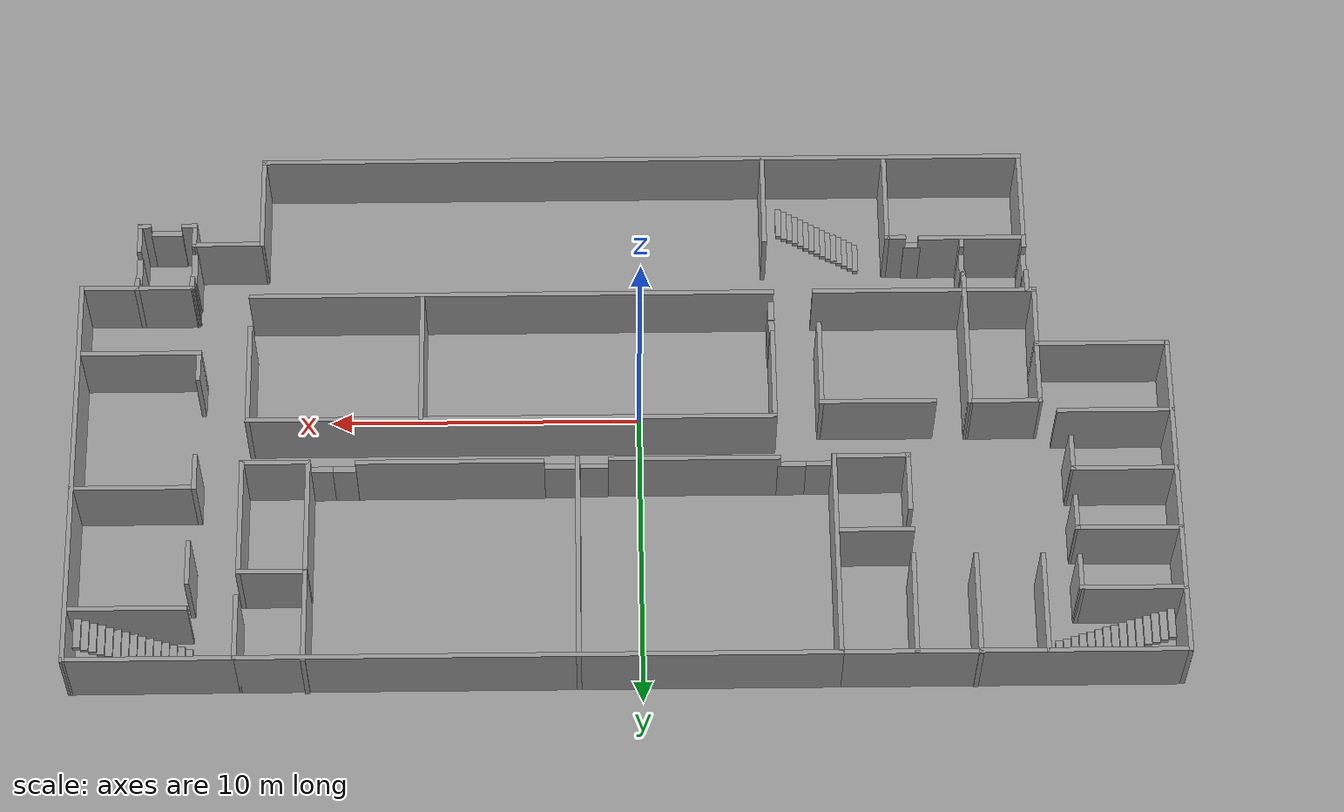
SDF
<sdf version="1.6">
 <world name="default">
  <light name="sun" type="directional">
   <pose>0 0 10 0 -0 0</pose>
   <diffuse>0.8 0.8 0.8 1</diffuse>
   <specular>0.2 0.2 0.2 1</specular>
   <attenuation>
    <range>1000</range>
    <constant>0.9</constant>
    <linear>0.01</linear>
    <quadratic>0.001</quadratic>
   </attenuation>
   <direction>0.5 0.1 -0.9</direction>
  </light>
  <scene><ambient>0.4 0.4 0.4 1</ambient><background>0.7 0.7 0.7 1</background><shadows>1</shadows></scene>
  <physics name="default_physics" default="0" type="ode">
   <max_step_size>0.01</max_step_size>
   <real_time_factor>1</real_time_factor>
   <real_time_update_rate>100</real_time_update_rate>
  </physics>
  <model name="ground_plane_0">
   <static>1</static>
   <link name="link">
    <collision name="collision">
     <geometry><plane><normal>0 0 1</normal><size>100 100</size></plane></geometry>
     <surface><friction><ode><mu>100</mu><mu2>50</mu2></ode></friction></surface>
    </collision>
    <visual name="visual">
     <cast_shadows>0</cast_shadows>
     <geometry><plane><normal>0 0 1</normal><size>100 100</size></plane></geometry>
     <material>
      <script><uri>file://media/materials/scripts/gazebo.material</uri><name>Gazebo/Grey</name></script>
     </material>
    </visual>
    <velocity_decay><linear>0</linear><angular>0</angular></velocity_decay>
   </link>
   <pose>0.497681 0 0 0 -0 0</pose>
  </model>
  <gravity>0 0 -9.8</gravity>
  <magnetic_field>6e-06 2.3e-05 -4.2e-05</magnetic_field>
  <atmosphere type="adiabatic"/>
  <spherical_coordinates>
   <surface_model>EARTH_WGS84</surface_model>
   <latitude_deg>0</latitude_deg>
   <longitude_deg>0</longitude_deg>
   <elevation>0</elevation>
   <heading_deg>0</heading_deg>
  </spherical_coordinates>
  <model name="Devon1st">
   <pose>0.529012 0.529264 0 0 -0 0</pose>
   <link name="Door_0">
    <collision name="Door_0_Collision">
     <geometry><box><size>0.9 0.17 2</size></box></geometry>
     <pose>0 0 1 0 -0 0</pose>
    </collision>
    <visual name="Door_0_Visual">
     <pose>0 0 1 0 -0 0</pose>
     <geometry><box><size>0.9 0.17 2</size></box></geometry>
     <material>
      <script><uri>file://media/materials/scripts/gazebo.material</uri><name>Gazebo/Grey</name></script>
     </material>
    </visual>
    <pose>0.962479 2.12819 0 0 -0 0</pose>
   </link>
   <link name="Door_1">
    <collision name="Door_1_Collision">
     <geometry><box><size>1.01304 0.2 2</size></box></geometry>
     <pose>0 0 1 0 -0 0</pose>
    </collision>
    <visual name="Door_1_Visual">
     <pose>0 0 1 0 -0 0</pose>
     <geometry><box><size>1.01304 0.2 2</size></box></geometry>
     <material>
      <script><uri>file://media/materials/scripts/gazebo.material</uri><name>Gazebo/Grey</name></script>
     </material>
    </visual>
    <pose>2.05919 2.13031 0 0 -0 0</pose>
   </link>
   <link name="Door_10">
    <collision name="Door_10_Collision">
     <geometry><box><size>0.9 0.17 2</size></box></geometry>
     <pose>0 0 1 0 -0 0</pose>
    </collision>
    <visual name="Door_10_Visual">
     <pose>0 0 1 0 -0 0</pose>
     <geometry><box><size>0.9 0.17 2</size></box></geometry>
     <material>
      <script><uri>file://media/materials/scripts/gazebo.material</uri><name>Gazebo/Grey</name></script>
     </material>
    </visual>
    <pose>-11.095 -5.06555 0 0 0 -1.57113</pose>
   </link>
   <link name="Door_11">
    <collision name="Door_11_Collision">
     <geometry><box><size>1.12 0.2 2</size></box></geometry>
     <pose>0 0 1 0 -0 0</pose>
    </collision>
    <visual name="Door_11_Visual">
     <pose>0 0 1 0 -0 0</pose>
     <geometry><box><size>1.12 0.2 2</size></box></geometry>
     <material>
      <script><uri>file://media/materials/scripts/gazebo.material</uri><name>Gazebo/Grey</name></script>
     </material>
    </visual>
    <pose>13.9457 -5.24793 0 0 -0 1.5708</pose>
   </link>
   <link name="Door_12">
    <collision name="Door_12_Collision">
     <geometry><box><size>1.0094 0.2 2</size></box></geometry>
     <pose>0 0 1 0 -0 0</pose>
    </collision>
    <visual name="Door_12_Visual">
     <pose>0 0 1 0 -0 0</pose>
     <geometry><box><size>1.0094 0.2 2</size></box></geometry>
     <material>
      <script><uri>file://media/materials/scripts/gazebo.material</uri><name>Gazebo/Grey</name></script>
     </material>
    </visual>
    <pose>15.7353 -5.11263 0 0 -0 1.56332</pose>
   </link>
   <link name="Door_13">
    <collision name="Door_13_Collision">
     <geometry><box><size>1.01 0.2 2</size></box></geometry>
     <pose>0 0 1 0 -0 0</pose>
    </collision>
    <visual name="Door_13_Visual">
     <pose>0 0 1 0 -0 0</pose>
     <geometry><box><size>1.01 0.2 2</size></box></geometry>
     <material>
      <script><uri>file://media/materials/scripts/gazebo.material</uri><name>Gazebo/Grey</name></script>
     </material>
    </visual>
    <pose>14.8957 -6.60293 0 0 -0 0</pose>
   </link>
   <link name="Door_2">
    <collision name="Door_2_Collision">
     <geometry><box><size>0.9 0.17 2</size></box></geometry>
     <pose>0 0 1 0 -0 0</pose>
    </collision>
    <visual name="Door_2_Visual">
     <pose>0 0 1 0 -0 0</pose>
     <geometry><box><size>0.9 0.17 2</size></box></geometry>
     <material>
      <script><uri>file://media/materials/scripts/gazebo.material</uri><name>Gazebo/Grey</name></script>
     </material>
    </visual>
    <pose>-6.22882 2.1021 0 0 -0 0</pose>
   </link>
   <link name="Door_3">
    <collision name="Door_3_Collision">
     <geometry><box><size>0.9 0.17 2</size></box></geometry>
     <pose>0 0 1 0 -0 0</pose>
    </collision>
    <visual name="Door_3_Visual">
     <pose>0 0 1 0 -0 0</pose>
     <geometry><box><size>0.9 0.17 2</size></box></geometry>
     <material>
      <script><uri>file://media/materials/scripts/gazebo.material</uri><name>Gazebo/Grey</name></script>
     </material>
    </visual>
    <pose>-5.34187 2.1195 0 0 -0 0</pose>
   </link>
   <link name="Door_4">
    <collision name="Door_4_Collision">
     <geometry><box><size>0.556948 0.2 2</size></box></geometry>
     <pose>0 0 1 0 -0 0</pose>
    </collision>
    <visual name="Door_4_Visual">
     <pose>0 0 1 0 -0 0</pose>
     <geometry><box><size>0.556948 0.2 2</size></box></geometry>
     <material>
      <script><uri>file://media/materials/scripts/gazebo.material</uri><name>Gazebo/Grey</name></script>
     </material>
    </visual>
    <pose>-9.50821 -5.91025 0 0 -0 0</pose>
   </link>
   <link name="Door_5">
    <collision name="Door_5_Collision">
     <geometry><box><size>0.745 0.2 2</size></box></geometry>
     <pose>0 0 1 0 -0 0</pose>
    </collision>
    <visual name="Door_5_Visual">
     <pose>0 0 1 0 -0 0</pose>
     <geometry><box><size>0.745 0.2 2</size></box></geometry>
     <material>
      <script><uri>file://media/materials/scripts/gazebo.material</uri><name>Gazebo/Grey</name></script>
     </material>
    </visual>
    <pose>8.90588 2.1621 0 0 -0 0</pose>
   </link>
   <link name="Door_6">
    <collision name="Door_6_Collision">
     <geometry><box><size>0.71 0.2 2</size></box></geometry>
     <pose>0 0 1 0 -0 0</pose>
    </collision>
    <visual name="Door_6_Visual">
     <pose>0 0 1 0 -0 0</pose>
     <geometry><box><size>0.71 0.2 2</size></box></geometry>
     <material>
      <script><uri>file://media/materials/scripts/gazebo.material</uri><name>Gazebo/Grey</name></script>
     </material>
    </visual>
    <pose>9.63338 2.1621 0 0 -0 0</pose>
   </link>
   <link name="Door_7">
    <collision name="Door_7_Collision">
     <geometry><box><size>0.631949 0.2 2</size></box></geometry>
     <pose>0 0 1 0 -0 0</pose>
    </collision>
    <visual name="Door_7_Visual">
     <pose>0 0 1 0 -0 0</pose>
     <geometry><box><size>0.631949 0.2 2</size></box></geometry>
     <material>
      <script><uri>file://media/materials/scripts/gazebo.material</uri><name>Gazebo/Grey</name></script>
     </material>
    </visual>
    <pose>-4.82459 -2.7964 0 0 0 -1.56264</pose>
   </link>
   <link name="Door_8">
    <collision name="Door_8_Collision">
     <geometry><box><size>0.695848 0.2 2</size></box></geometry>
     <pose>0 0 1 0 -0 0</pose>
    </collision>
    <visual name="Door_8_Visual">
     <pose>0 0 1 0 -0 0</pose>
     <geometry><box><size>0.695848 0.2 2</size></box></geometry>
     <material>
      <script><uri>file://media/materials/scripts/gazebo.material</uri><name>Gazebo/Grey</name></script>
     </material>
    </visual>
    <pose>-4.83152 -3.47647 0 0 0 -1.58327</pose>
   </link>
   <link name="Door_9">
    <collision name="Door_9_Collision">
     <geometry><box><size>0.9 0.17 2</size></box></geometry>
     <pose>0 0 1 0 -0 0</pose>
    </collision>
    <visual name="Door_9_Visual">
     <pose>0 0 1 0 -0 0</pose>
     <geometry><box><size>0.9 0.17 2</size></box></geometry>
     <material>
      <script><uri>file://media/materials/scripts/gazebo.material</uri><name>Gazebo/Grey</name></script>
     </material>
    </visual>
    <pose>-13.1241 -5.08705 0 0 0 -1.55889</pose>
   </link>
   <link name="Stairs_2">
    <visual name="Stairs_2_Visual_0">
     <pose>-7.74491 -6.50403 0.083333 0 -0 1.5708</pose>
     <geometry><box><size>1 0.187333 0.166667</size></box></geometry>
     <material>
      <script><uri>file://media/materials/scripts/gazebo.material</uri><name>Gazebo/Grey</name></script>
      <ambient>1 1 1 1</ambient>
     </material>
    </visual>
    <collision name="Stairs_2_Collision_0">
     <geometry><box><size>1 0.187333 0.166667</size></box></geometry>
     <pose>-7.74491 -6.50403 0.083333 0 -0 1.5708</pose>
    </collision>
    <visual name="Stairs_2_Visual_1">
     <pose>-7.55758 -6.50403 0.25 0 -0 1.5708</pose>
     <geometry><box><size>1 0.187333 0.166667</size></box></geometry>
     <material>
      <script><uri>file://media/materials/scripts/gazebo.material</uri><name>Gazebo/Grey</name></script>
      <ambient>1 1 1 1</ambient>
     </material>
    </visual>
    <collision name="Stairs_2_Collision_1">
     <geometry><box><size>1 0.187333 0.166667</size></box></geometry>
     <pose>-7.55758 -6.50403 0.25 0 -0 1.5708</pose>
    </collision>
    <visual name="Stairs_2_Visual_2">
     <pose>-7.37024 -6.50403 0.416667 0 -0 1.5708</pose>
     <geometry><box><size>1 0.187333 0.166667</size></box></geometry>
     <material>
      <script><uri>file://media/materials/scripts/gazebo.material</uri><name>Gazebo/Grey</name></script>
      <ambient>1 1 1 1</ambient>
     </material>
    </visual>
    <collision name="Stairs_2_Collision_2">
     <geometry><box><size>1 0.187333 0.166667</size></box></geometry>
     <pose>-7.37024 -6.50403 0.416667 0 -0 1.5708</pose>
    </collision>
    <visual name="Stairs_2_Visual_3">
     <pose>-7.18291 -6.50403 0.583333 0 -0 1.5708</pose>
     <geometry><box><size>1 0.187333 0.166667</size></box></geometry>
     <material>
      <script><uri>file://media/materials/scripts/gazebo.material</uri><name>Gazebo/Grey</name></script>
      <ambient>1 1 1 1</ambient>
     </material>
    </visual>
    <collision name="Stairs_2_Collision_3">
     <geometry><box><size>1 0.187333 0.166667</size></box></geometry>
     <pose>-7.18291 -6.50403 0.583333 0 -0 1.5708</pose>
    </collision>
    <visual name="Stairs_2_Visual_4">
     <pose>-6.99558 -6.50403 0.75 0 -0 1.5708</pose>
     <geometry><box><size>1 0.187333 0.166667</size></box></geometry>
     <material>
      <script><uri>file://media/materials/scripts/gazebo.material</uri><name>Gazebo/Grey</name></script>
      <ambient>1 1 1 1</ambient>
     </material>
    </visual>
    <collision name="Stairs_2_Collision_4">
     <geometry><box><size>1 0.187333 0.166667</size></box></geometry>
     <pose>-6.99558 -6.50403 0.75 0 -0 1.5708</pose>
    </collision>
    <visual name="Stairs_2_Visual_5">
     <pose>-6.80824 -6.50403 0.916667 0 -0 1.5708</pose>
     <geometry><box><size>1 0.187333 0.166667</size></box></geometry>
     <material>
      <script><uri>file://media/materials/scripts/gazebo.material</uri><name>Gazebo/Grey</name></script>
      <ambient>1 1 1 1</ambient>
     </material>
    </visual>
    <collision name="Stairs_2_Collision_5">
     <geometry><box><size>1 0.187333 0.166667</size></box></geometry>
     <pose>-6.80824 -6.50403 0.916667 0 -0 1.5708</pose>
    </collision>
    <visual name="Stairs_2_Visual_6">
     <pose>-6.62091 -6.50403 1.08333 0 -0 1.5708</pose>
     <geometry><box><size>1 0.187333 0.166667</size></box></geometry>
     <material>
      <script><uri>file://media/materials/scripts/gazebo.material</uri><name>Gazebo/Grey</name></script>
      <ambient>1 1 1 1</ambient>
     </material>
    </visual>
    <collision name="Stairs_2_Collision_6">
     <geometry><box><size>1 0.187333 0.166667</size></box></geometry>
     <pose>-6.62091 -6.50403 1.08333 0 -0 1.5708</pose>
    </collision>
    <visual name="Stairs_2_Visual_7">
     <pose>-6.43358 -6.50403 1.25 0 -0 1.5708</pose>
     <geometry><box><size>1 0.187333 0.166667</size></box></geometry>
     <material>
      <script><uri>file://media/materials/scripts/gazebo.material</uri><name>Gazebo/Grey</name></script>
      <ambient>1 1 1 1</ambient>
     </material>
    </visual>
    <collision name="Stairs_2_Collision_7">
     <geometry><box><size>1 0.187333 0.166667</size></box></geometry>
     <pose>-6.43358 -6.50403 1.25 0 -0 1.5708</pose>
    </collision>
    <visual name="Stairs_2_Visual_8">
     <pose>-6.24624 -6.50403 1.41667 0 -0 1.5708</pose>
     <geometry><box><size>1 0.187333 0.166667</size></box></geometry>
     <material>
      <script><uri>file://media/materials/scripts/gazebo.material</uri><name>Gazebo/Grey</name></script>
      <ambient>1 1 1 1</ambient>
     </material>
    </visual>
    <collision name="Stairs_2_Collision_8">
     <geometry><box><size>1 0.187333 0.166667</size></box></geometry>
     <pose>-6.24624 -6.50403 1.41667 0 -0 1.5708</pose>
    </collision>
    <visual name="Stairs_2_Visual_9">
     <pose>-6.05891 -6.50403 1.58333 0 -0 1.5708</pose>
     <geometry><box><size>1 0.187333 0.166667</size></box></geometry>
     <material>
      <script><uri>file://media/materials/scripts/gazebo.material</uri><name>Gazebo/Grey</name></script>
      <ambient>1 1 1 1</ambient>
     </material>
    </visual>
    <collision name="Stairs_2_Collision_9">
     <geometry><box><size>1 0.187333 0.166667</size></box></geometry>
     <pose>-6.05891 -6.50403 1.58333 0 -0 1.5708</pose>
    </collision>
    <visual name="Stairs_2_Visual_10">
     <pose>-5.87158 -6.50403 1.75 0 -0 1.5708</pose>
     <geometry><box><size>1 0.187333 0.166667</size></box></geometry>
     <material>
      <script><uri>file://media/materials/scripts/gazebo.material</uri><name>Gazebo/Grey</name></script>
      <ambient>1 1 1 1</ambient>
     </material>
    </visual>
    <collision name="Stairs_2_Collision_10">
     <geometry><box><size>1 0.187333 0.166667</size></box></geometry>
     <pose>-5.87158 -6.50403 1.75 0 -0 1.5708</pose>
    </collision>
    <visual name="Stairs_2_Visual_11">
     <pose>-5.68424 -6.50403 1.91667 0 -0 1.5708</pose>
     <geometry><box><size>1 0.187333 0.166667</size></box></geometry>
     <material>
      <script><uri>file://media/materials/scripts/gazebo.material</uri><name>Gazebo/Grey</name></script>
      <ambient>1 1 1 1</ambient>
     </material>
    </visual>
    <collision name="Stairs_2_Collision_11">
     <geometry><box><size>1 0.187333 0.166667</size></box></geometry>
     <pose>-5.68424 -6.50403 1.91667 0 -0 1.5708</pose>
    </collision>
    <visual name="Stairs_2_Visual_12">
     <pose>-5.49691 -6.50403 2.08333 0 -0 1.5708</pose>
     <geometry><box><size>1 0.187333 0.166667</size></box></geometry>
     <material>
      <script><uri>file://media/materials/scripts/gazebo.material</uri><name>Gazebo/Grey</name></script>
      <ambient>1 1 1 1</ambient>
     </material>
    </visual>
    <collision name="Stairs_2_Collision_12">
     <geometry><box><size>1 0.187333 0.166667</size></box></geometry>
     <pose>-5.49691 -6.50403 2.08333 0 -0 1.5708</pose>
    </collision>
    <visual name="Stairs_2_Visual_13">
     <pose>-5.30958 -6.50403 2.25 0 -0 1.5708</pose>
     <geometry><box><size>1 0.187333 0.166667</size></box></geometry>
     <material>
      <script><uri>file://media/materials/scripts/gazebo.material</uri><name>Gazebo/Grey</name></script>
      <ambient>1 1 1 1</ambient>
     </material>
    </visual>
    <collision name="Stairs_2_Collision_13">
     <geometry><box><size>1 0.187333 0.166667</size></box></geometry>
     <pose>-5.30958 -6.50403 2.25 0 -0 1.5708</pose>
    </collision>
    <visual name="Stairs_2_Visual_14">
     <pose>-5.12224 -6.50403 2.41667 0 -0 1.5708</pose>
     <geometry><box><size>1 0.187333 0.166667</size></box></geometry>
     <material>
      <script><uri>file://media/materials/scripts/gazebo.material</uri><name>Gazebo/Grey</name></script>
      <ambient>1 1 1 1</ambient>
     </material>
    </visual>
    <collision name="Stairs_2_Collision_14">
     <geometry><box><size>1 0.187333 0.166667</size></box></geometry>
     <pose>-5.12224 -6.50403 2.41667 0 -0 1.5708</pose>
    </collision>
   </link>
   <link name="Stairs_3">
    <visual name="Stairs_3_Visual_0">
     <pose>13.8125 8.06468 0.083333 0 -0 1.5708</pose>
     <geometry><box><size>1 0.233333 0.166667</size></box></geometry>
     <material>
      <script><uri>file://media/materials/scripts/gazebo.material</uri><name>Gazebo/Grey</name></script>
      <ambient>1 1 1 1</ambient>
     </material>
    </visual>
    <collision name="Stairs_3_Collision_0">
     <geometry><box><size>1 0.233333 0.166667</size></box></geometry>
     <pose>13.8125 8.06468 0.083333 0 -0 1.5708</pose>
    </collision>
    <visual name="Stairs_3_Visual_1">
     <pose>14.0458 8.06468 0.25 0 -0 1.5708</pose>
     <geometry><box><size>1 0.233333 0.166667</size></box></geometry>
     <material>
      <script><uri>file://media/materials/scripts/gazebo.material</uri><name>Gazebo/Grey</name></script>
      <ambient>1 1 1 1</ambient>
     </material>
    </visual>
    <collision name="Stairs_3_Collision_1">
     <geometry><box><size>1 0.233333 0.166667</size></box></geometry>
     <pose>14.0458 8.06468 0.25 0 -0 1.5708</pose>
    </collision>
    <visual name="Stairs_3_Visual_2">
     <pose>14.2792 8.06468 0.416667 0 -0 1.5708</pose>
     <geometry><box><size>1 0.233333 0.166667</size></box></geometry>
     <material>
      <script><uri>file://media/materials/scripts/gazebo.material</uri><name>Gazebo/Grey</name></script>
      <ambient>1 1 1 1</ambient>
     </material>
    </visual>
    <collision name="Stairs_3_Collision_2">
     <geometry><box><size>1 0.233333 0.166667</size></box></geometry>
     <pose>14.2792 8.06468 0.416667 0 -0 1.5708</pose>
    </collision>
    <visual name="Stairs_3_Visual_3">
     <pose>14.5125 8.06468 0.583333 0 -0 1.5708</pose>
     <geometry><box><size>1 0.233333 0.166667</size></box></geometry>
     <material>
      <script><uri>file://media/materials/scripts/gazebo.material</uri><name>Gazebo/Grey</name></script>
      <ambient>1 1 1 1</ambient>
     </material>
    </visual>
    <collision name="Stairs_3_Collision_3">
     <geometry><box><size>1 0.233333 0.166667</size></box></geometry>
     <pose>14.5125 8.06468 0.583333 0 -0 1.5708</pose>
    </collision>
    <visual name="Stairs_3_Visual_4">
     <pose>14.7458 8.06468 0.75 0 -0 1.5708</pose>
     <geometry><box><size>1 0.233333 0.166667</size></box></geometry>
     <material>
      <script><uri>file://media/materials/scripts/gazebo.material</uri><name>Gazebo/Grey</name></script>
      <ambient>1 1 1 1</ambient>
     </material>
    </visual>
    <collision name="Stairs_3_Collision_4">
     <geometry><box><size>1 0.233333 0.166667</size></box></geometry>
     <pose>14.7458 8.06468 0.75 0 -0 1.5708</pose>
    </collision>
    <visual name="Stairs_3_Visual_5">
     <pose>14.9792 8.06468 0.916667 0 -0 1.5708</pose>
     <geometry><box><size>1 0.233333 0.166667</size></box></geometry>
     <material>
      <script><uri>file://media/materials/scripts/gazebo.material</uri><name>Gazebo/Grey</name></script>
      <ambient>1 1 1 1</ambient>
     </material>
    </visual>
    <collision name="Stairs_3_Collision_5">
     <geometry><box><size>1 0.233333 0.166667</size></box></geometry>
     <pose>14.9792 8.06468 0.916667 0 -0 1.5708</pose>
    </collision>
    <visual name="Stairs_3_Visual_6">
     <pose>15.2125 8.06468 1.08333 0 -0 1.5708</pose>
     <geometry><box><size>1 0.233333 0.166667</size></box></geometry>
     <material>
      <script><uri>file://media/materials/scripts/gazebo.material</uri><name>Gazebo/Grey</name></script>
      <ambient>1 1 1 1</ambient>
     </material>
    </visual>
    <collision name="Stairs_3_Collision_6">
     <geometry><box><size>1 0.233333 0.166667</size></box></geometry>
     <pose>15.2125 8.06468 1.08333 0 -0 1.5708</pose>
    </collision>
    <visual name="Stairs_3_Visual_7">
     <pose>15.4458 8.06468 1.25 0 -0 1.5708</pose>
     <geometry><box><size>1 0.233333 0.166667</size></box></geometry>
     <material>
      <script><uri>file://media/materials/scripts/gazebo.material</uri><name>Gazebo/Grey</name></script>
      <ambient>1 1 1 1</ambient>
     </material>
    </visual>
    <collision name="Stairs_3_Collision_7">
     <geometry><box><size>1 0.233333 0.166667</size></box></geometry>
     <pose>15.4458 8.06468 1.25 0 -0 1.5708</pose>
    </collision>
    <visual name="Stairs_3_Visual_8">
     <pose>15.6792 8.06468 1.41667 0 -0 1.5708</pose>
     <geometry><box><size>1 0.233333 0.166667</size></box></geometry>
     <material>
      <script><uri>file://media/materials/scripts/gazebo.material</uri><name>Gazebo/Grey</name></script>
      <ambient>1 1 1 1</ambient>
     </material>
    </visual>
    <collision name="Stairs_3_Collision_8">
     <geometry><box><size>1 0.233333 0.166667</size></box></geometry>
     <pose>15.6792 8.06468 1.41667 0 -0 1.5708</pose>
    </collision>
    <visual name="Stairs_3_Visual_9">
     <pose>15.9125 8.06468 1.58333 0 -0 1.5708</pose>
     <geometry><box><size>1 0.233333 0.166667</size></box></geometry>
     <material>
      <script><uri>file://media/materials/scripts/gazebo.material</uri><name>Gazebo/Grey</name></script>
      <ambient>1 1 1 1</ambient>
     </material>
    </visual>
    <collision name="Stairs_3_Collision_9">
     <geometry><box><size>1 0.233333 0.166667</size></box></geometry>
     <pose>15.9125 8.06468 1.58333 0 -0 1.5708</pose>
    </collision>
    <visual name="Stairs_3_Visual_10">
     <pose>16.1458 8.06468 1.75 0 -0 1.5708</pose>
     <geometry><box><size>1 0.233333 0.166667</size></box></geometry>
     <material>
      <script><uri>file://media/materials/scripts/gazebo.material</uri><name>Gazebo/Grey</name></script>
      <ambient>1 1 1 1</ambient>
     </material>
    </visual>
    <collision name="Stairs_3_Collision_10">
     <geometry><box><size>1 0.233333 0.166667</size></box></geometry>
     <pose>16.1458 8.06468 1.75 0 -0 1.5708</pose>
    </collision>
    <visual name="Stairs_3_Visual_11">
     <pose>16.3792 8.06468 1.91667 0 -0 1.5708</pose>
     <geometry><box><size>1 0.233333 0.166667</size></box></geometry>
     <material>
      <script><uri>file://media/materials/scripts/gazebo.material</uri><name>Gazebo/Grey</name></script>
      <ambient>1 1 1 1</ambient>
     </material>
    </visual>
    <collision name="Stairs_3_Collision_11">
     <geometry><box><size>1 0.233333 0.166667</size></box></geometry>
     <pose>16.3792 8.06468 1.91667 0 -0 1.5708</pose>
    </collision>
    <visual name="Stairs_3_Visual_12">
     <pose>16.6125 8.06468 2.08333 0 -0 1.5708</pose>
     <geometry><box><size>1 0.233333 0.166667</size></box></geometry>
     <material>
      <script><uri>file://media/materials/scripts/gazebo.material</uri><name>Gazebo/Grey</name></script>
      <ambient>1 1 1 1</ambient>
     </material>
    </visual>
    <collision name="Stairs_3_Collision_12">
     <geometry><box><size>1 0.233333 0.166667</size></box></geometry>
     <pose>16.6125 8.06468 2.08333 0 -0 1.5708</pose>
    </collision>
    <visual name="Stairs_3_Visual_13">
     <pose>16.8458 8.06468 2.25 0 -0 1.5708</pose>
     <geometry><box><size>1 0.233333 0.166667</size></box></geometry>
     <material>
      <script><uri>file://media/materials/scripts/gazebo.material</uri><name>Gazebo/Grey</name></script>
      <ambient>1 1 1 1</ambient>
     </material>
    </visual>
    <collision name="Stairs_3_Collision_13">
     <geometry><box><size>1 0.233333 0.166667</size></box></geometry>
     <pose>16.8458 8.06468 2.25 0 -0 1.5708</pose>
    </collision>
    <visual name="Stairs_3_Visual_14">
     <pose>17.0792 8.06468 2.41667 0 -0 1.5708</pose>
     <geometry><box><size>1 0.233333 0.166667</size></box></geometry>
     <material>
      <script><uri>file://media/materials/scripts/gazebo.material</uri><name>Gazebo/Grey</name></script>
      <ambient>1 1 1 1</ambient>
     </material>
    </visual>
    <collision name="Stairs_3_Collision_14">
     <geometry><box><size>1 0.233333 0.166667</size></box></geometry>
     <pose>17.0792 8.06468 2.41667 0 -0 1.5708</pose>
    </collision>
   </link>
   <link name="Stairs_4">
    <visual name="Stairs_4_Visual_0">
     <pose>-13.7119 8.07177 0.083333 0 -0 -1.5708</pose>
     <geometry><box><size>1 0.233333 0.166667</size></box></geometry>
     <material>
      <script><uri>file://media/materials/scripts/gazebo.material</uri><name>Gazebo/Grey</name></script>
      <ambient>1 1 1 1</ambient>
     </material>
    </visual>
    <collision name="Stairs_4_Collision_0">
     <geometry><box><size>1 0.233333 0.166667</size></box></geometry>
     <pose>-13.7119 8.07177 0.083333 0 -0 -1.5708</pose>
    </collision>
    <visual name="Stairs_4_Visual_1">
     <pose>-13.9452 8.07177 0.25 0 -0 -1.5708</pose>
     <geometry><box><size>1 0.233333 0.166667</size></box></geometry>
     <material>
      <script><uri>file://media/materials/scripts/gazebo.material</uri><name>Gazebo/Grey</name></script>
      <ambient>1 1 1 1</ambient>
     </material>
    </visual>
    <collision name="Stairs_4_Collision_1">
     <geometry><box><size>1 0.233333 0.166667</size></box></geometry>
     <pose>-13.9452 8.07177 0.25 0 -0 -1.5708</pose>
    </collision>
    <visual name="Stairs_4_Visual_2">
     <pose>-14.1786 8.07177 0.416667 0 -0 -1.5708</pose>
     <geometry><box><size>1 0.233333 0.166667</size></box></geometry>
     <material>
      <script><uri>file://media/materials/scripts/gazebo.material</uri><name>Gazebo/Grey</name></script>
      <ambient>1 1 1 1</ambient>
     </material>
    </visual>
    <collision name="Stairs_4_Collision_2">
     <geometry><box><size>1 0.233333 0.166667</size></box></geometry>
     <pose>-14.1786 8.07177 0.416667 0 -0 -1.5708</pose>
    </collision>
    <visual name="Stairs_4_Visual_3">
     <pose>-14.4119 8.07177 0.583333 0 -0 -1.5708</pose>
     <geometry><box><size>1 0.233333 0.166667</size></box></geometry>
     <material>
      <script><uri>file://media/materials/scripts/gazebo.material</uri><name>Gazebo/Grey</name></script>
      <ambient>1 1 1 1</ambient>
     </material>
    </visual>
    <collision name="Stairs_4_Collision_3">
     <geometry><box><size>1 0.233333 0.166667</size></box></geometry>
     <pose>-14.4119 8.07177 0.583333 0 -0 -1.5708</pose>
    </collision>
    <visual name="Stairs_4_Visual_4">
     <pose>-14.6452 8.07177 0.75 0 -0 -1.5708</pose>
     <geometry><box><size>1 0.233333 0.166667</size></box></geometry>
     <material>
      <script><uri>file://media/materials/scripts/gazebo.material</uri><name>Gazebo/Grey</name></script>
      <ambient>1 1 1 1</ambient>
     </material>
    </visual>
    <collision name="Stairs_4_Collision_4">
     <geometry><box><size>1 0.233333 0.166667</size></box></geometry>
     <pose>-14.6452 8.07177 0.75 0 -0 -1.5708</pose>
    </collision>
    <visual name="Stairs_4_Visual_5">
     <pose>-14.8786 8.07177 0.916667 0 -0 -1.5708</pose>
     <geometry><box><size>1 0.233333 0.166667</size></box></geometry>
     <material>
      <script><uri>file://media/materials/scripts/gazebo.material</uri><name>Gazebo/Grey</name></script>
      <ambient>1 1 1 1</ambient>
     </material>
    </visual>
    <collision name="Stairs_4_Collision_5">
     <geometry><box><size>1 0.233333 0.166667</size></box></geometry>
     <pose>-14.8786 8.07177 0.916667 0 -0 -1.5708</pose>
    </collision>
    <visual name="Stairs_4_Visual_6">
     <pose>-15.1119 8.07177 1.08333 0 -0 -1.5708</pose>
     <geometry><box><size>1 0.233333 0.166667</size></box></geometry>
     <material>
      <script><uri>file://media/materials/scripts/gazebo.material</uri><name>Gazebo/Grey</name></script>
      <ambient>1 1 1 1</ambient>
     </material>
    </visual>
    <collision name="Stairs_4_Collision_6">
     <geometry><box><size>1 0.233333 0.166667</size></box></geometry>
     <pose>-15.1119 8.07177 1.08333 0 -0 -1.5708</pose>
    </collision>
    <visual name="Stairs_4_Visual_7">
     <pose>-15.3452 8.07177 1.25 0 -0 -1.5708</pose>
     <geometry><box><size>1 0.233333 0.166667</size></box></geometry>
     <material>
      <script><uri>file://media/materials/scripts/gazebo.material</uri><name>Gazebo/Grey</name></script>
      <ambient>1 1 1 1</ambient>
     </material>
    </visual>
    <collision name="Stairs_4_Collision_7">
     <geometry><box><size>1 0.233333 0.166667</size></box></geometry>
     <pose>-15.3452 8.07177 1.25 0 -0 -1.5708</pose>
    </collision>
    <visual name="Stairs_4_Visual_8">
     <pose>-15.5786 8.07177 1.41667 0 -0 -1.5708</pose>
     <geometry><box><size>1 0.233333 0.166667</size></box></geometry>
     <material>
      <script><uri>file://media/materials/scripts/gazebo.material</uri><name>Gazebo/Grey</name></script>
      <ambient>1 1 1 1</ambient>
     </material>
    </visual>
    <collision name="Stairs_4_Collision_8">
     <geometry><box><size>1 0.233333 0.166667</size></box></geometry>
     <pose>-15.5786 8.07177 1.41667 0 -0 -1.5708</pose>
    </collision>
    <visual name="Stairs_4_Visual_9">
     <pose>-15.8119 8.07177 1.58333 0 -0 -1.5708</pose>
     <geometry><box><size>1 0.233333 0.166667</size></box></geometry>
     <material>
      <script><uri>file://media/materials/scripts/gazebo.material</uri><name>Gazebo/Grey</name></script>
      <ambient>1 1 1 1</ambient>
     </material>
    </visual>
    <collision name="Stairs_4_Collision_9">
     <geometry><box><size>1 0.233333 0.166667</size></box></geometry>
     <pose>-15.8119 8.07177 1.58333 0 -0 -1.5708</pose>
    </collision>
    <visual name="Stairs_4_Visual_10">
     <pose>-16.0452 8.07177 1.75 0 -0 -1.5708</pose>
     <geometry><box><size>1 0.233333 0.166667</size></box></geometry>
     <material>
      <script><uri>file://media/materials/scripts/gazebo.material</uri><name>Gazebo/Grey</name></script>
      <ambient>1 1 1 1</ambient>
     </material>
    </visual>
    <collision name="Stairs_4_Collision_10">
     <geometry><box><size>1 0.233333 0.166667</size></box></geometry>
     <pose>-16.0452 8.07177 1.75 0 -0 -1.5708</pose>
    </collision>
    <visual name="Stairs_4_Visual_11">
     <pose>-16.2786 8.07177 1.91667 0 -0 -1.5708</pose>
     <geometry><box><size>1 0.233333 0.166667</size></box></geometry>
     <material>
      <script><uri>file://media/materials/scripts/gazebo.material</uri><name>Gazebo/Grey</name></script>
      <ambient>1 1 1 1</ambient>
     </material>
    </visual>
    <collision name="Stairs_4_Collision_11">
     <geometry><box><size>1 0.233333 0.166667</size></box></geometry>
     <pose>-16.2786 8.07177 1.91667 0 -0 -1.5708</pose>
    </collision>
    <visual name="Stairs_4_Visual_12">
     <pose>-16.5119 8.07177 2.08333 0 -0 -1.5708</pose>
     <geometry><box><size>1 0.233333 0.166667</size></box></geometry>
     <material>
      <script><uri>file://media/materials/scripts/gazebo.material</uri><name>Gazebo/Grey</name></script>
      <ambient>1 1 1 1</ambient>
     </material>
    </visual>
    <collision name="Stairs_4_Collision_12">
     <geometry><box><size>1 0.233333 0.166667</size></box></geometry>
     <pose>-16.5119 8.07177 2.08333 0 -0 -1.5708</pose>
    </collision>
    <visual name="Stairs_4_Visual_13">
     <pose>-16.7452 8.07177 2.25 0 -0 -1.5708</pose>
     <geometry><box><size>1 0.233333 0.166667</size></box></geometry>
     <material>
      <script><uri>file://media/materials/scripts/gazebo.material</uri><name>Gazebo/Grey</name></script>
      <ambient>1 1 1 1</ambient>
     </material>
    </visual>
    <collision name="Stairs_4_Collision_13">
     <geometry><box><size>1 0.233333 0.166667</size></box></geometry>
     <pose>-16.7452 8.07177 2.25 0 -0 -1.5708</pose>
    </collision>
    <visual name="Stairs_4_Visual_14">
     <pose>-16.9786 8.07177 2.41667 0 -0 -1.5708</pose>
     <geometry><box><size>1 0.233333 0.166667</size></box></geometry>
     <material>
      <script><uri>file://media/materials/scripts/gazebo.material</uri><name>Gazebo/Grey</name></script>
      <ambient>1 1 1 1</ambient>
     </material>
    </visual>
    <collision name="Stairs_4_Collision_14">
     <geometry><box><size>1 0.233333 0.166667</size></box></geometry>
     <pose>-16.9786 8.07177 2.41667 0 -0 -1.5708</pose>
    </collision>
   </link>
   <link name="Wall_0">
    <collision name="Wall_0_Collision">
     <geometry><box><size>11 0.15 2.5</size></box></geometry>
     <pose>0 0 1.25 0 -0 0</pose>
    </collision>
    <visual name="Wall_0_Visual">
     <pose>0 0 1.25 0 -0 0</pose>
     <geometry><box><size>11 0.15 2.5</size></box></geometry>
     <material>
      <script><uri>file://media/materials/scripts/gazebo.material</uri><name>Gazebo/Grey</name></script>
      <ambient>1 1 1 1</ambient>
     </material>
    </visual>
    <pose>-17.5209 3.52191 0 0 0 -1.5708</pose>
   </link>
   <link name="Wall_1">
    <collision name="Wall_1_Collision">
     <geometry><box><size>4.32937 0.15 2.5</size></box></geometry>
     <pose>0 0 1.25 0 -0 0</pose>
    </collision>
    <visual name="Wall_1_Visual">
     <pose>0 0 1.25 0 -0 0</pose>
     <geometry><box><size>4.32937 0.15 2.5</size></box></geometry>
     <material>
      <script><uri>file://media/materials/scripts/gazebo.material</uri><name>Gazebo/Grey</name></script>
      <ambient>1 1 1 1</ambient>
     </material>
    </visual>
    <pose>-15.4313 -1.9097 0 0 0 -0.003164</pose>
   </link>
   <link name="Wall_102">
    <collision name="Wall_102_Collision">
     <geometry><box><size>0.770084 0.15 2.5</size></box></geometry>
     <pose>0 0 1.25 0 -0 0</pose>
    </collision>
    <visual name="Wall_102_Visual">
     <pose>0 0 1.25 0 -0 0</pose>
     <geometry><box><size>0.770084 0.15 2.5</size></box></geometry>
     <material>
      <script><uri>file://media/materials/scripts/gazebo.material</uri><name>Gazebo/Grey</name></script>
      <ambient>1 1 1 1</ambient>
     </material>
    </visual>
    <pose>-13.1337 -4.25789 0 0 0 -1.58299</pose>
   </link>
   <link name="Wall_105">
    <collision name="Wall_105_Collision">
     <geometry><box><size>4 0.15 2.5</size></box></geometry>
     <pose>0 0 1.25 0 -0 0</pose>
    </collision>
    <visual name="Wall_105_Visual">
     <pose>0 0 1.25 0 -0 0</pose>
     <geometry><box><size>4 0.15 2.5</size></box></geometry>
     <material>
      <script><uri>file://media/materials/scripts/gazebo.material</uri><name>Gazebo/Grey</name></script>
      <ambient>1 1 1 1</ambient>
     </material>
    </visual>
    <pose>15.5593 -1.85561 0 0 -0 0</pose>
   </link>
   <link name="Wall_107">
    <collision name="Wall_107_Collision">
     <geometry><box><size>1.25 0.15 2.5</size></box></geometry>
     <pose>0 0 1.25 0 -0 0</pose>
    </collision>
    <visual name="Wall_107_Visual">
     <pose>0 0 1.25 0 -0 0</pose>
     <geometry><box><size>1.25 0.15 2.5</size></box></geometry>
     <material>
      <script><uri>file://media/materials/scripts/gazebo.material</uri><name>Gazebo/Grey</name></script>
      <ambient>1 1 1 1</ambient>
     </material>
    </visual>
    <pose>13.6356 2.45036 0 0 0 -1.5708</pose>
   </link>
   <link name="Wall_109">
    <collision name="Wall_109_Collision">
     <geometry><box><size>1.07007 0.15 2.5</size></box></geometry>
     <pose>0 0 1.25 0 -0 0</pose>
    </collision>
    <visual name="Wall_109_Visual">
     <pose>0 0 1.25 0 -0 0</pose>
     <geometry><box><size>1.07007 0.15 2.5</size></box></geometry>
     <material>
      <script><uri>file://media/materials/scripts/gazebo.material</uri><name>Gazebo/Grey</name></script>
      <ambient>1 1 1 1</ambient>
     </material>
    </visual>
    <pose>13.6401 -1.39561 0 0 0 -1.5833</pose>
   </link>
   <link name="Wall_11">
    <collision name="Wall_11_Collision">
     <geometry><box><size>2.40851 0.15 2.5</size></box></geometry>
     <pose>0 0 1.25 0 -0 0</pose>
    </collision>
    <visual name="Wall_11_Visual">
     <pose>0 0 1.25 0 -0 0</pose>
     <geometry><box><size>2.40851 0.15 2.5</size></box></geometry>
     <material>
      <script><uri>file://media/materials/scripts/gazebo.material</uri><name>Gazebo/Grey</name></script>
      <ambient>1 1 1 1</ambient>
     </material>
    </visual>
    <pose>-12.2282 -3.92065 0 0 -0 3.13474</pose>
   </link>
   <link name="Wall_112">
    <collision name="Wall_112_Collision">
     <geometry><box><size>0.867664 0.15 2.5</size></box></geometry>
     <pose>0 0 1.25 0 -0 0</pose>
    </collision>
    <visual name="Wall_112_Visual">
     <pose>0 0 1.25 0 -0 0</pose>
     <geometry><box><size>0.867664 0.15 2.5</size></box></geometry>
     <material>
      <script><uri>file://media/materials/scripts/gazebo.material</uri><name>Gazebo/Grey</name></script>
      <ambient>1 1 1 1</ambient>
     </material>
    </visual>
    <pose>13.9429 -6.24406 0 0 0 -1.5708</pose>
   </link>
   <link name="Wall_113">
    <collision name="Wall_113_Collision">
     <geometry><box><size>0.513155 0.15 2.5</size></box></geometry>
     <pose>0 0 1.25 0 -0 0</pose>
    </collision>
    <visual name="Wall_113_Visual">
     <pose>0 0 1.25 0 -0 0</pose>
     <geometry><box><size>0.513155 0.15 2.5</size></box></geometry>
     <material>
      <script><uri>file://media/materials/scripts/gazebo.material</uri><name>Gazebo/Grey</name></script>
      <ambient>1 1 1 1</ambient>
     </material>
    </visual>
    <pose>14.1245 -6.6029 0 0 -0 0</pose>
   </link>
   <link name="Wall_115">
    <collision name="Wall_115_Collision">
     <geometry><box><size>0.469922 0.15 2.5</size></box></geometry>
     <pose>0 0 1.25 0 -0 0</pose>
    </collision>
    <visual name="Wall_115_Visual">
     <pose>0 0 1.25 0 -0 0</pose>
     <geometry><box><size>0.469922 0.15 2.5</size></box></geometry>
     <material>
      <script><uri>file://media/materials/scripts/gazebo.material</uri><name>Gazebo/Grey</name></script>
      <ambient>1 1 1 1</ambient>
     </material>
    </visual>
    <pose>13.9602 -4.45423 0 0 -0 1.5708</pose>
   </link>
   <link name="Wall_116">
    <collision name="Wall_116_Collision">
     <geometry><box><size>0.15 0.15 2.5</size></box></geometry>
     <pose>0 0 1.25 0 -0 0</pose>
    </collision>
    <visual name="Wall_116_Visual">
     <pose>0 0 1.25 0 -0 0</pose>
     <geometry><box><size>0.15 0.15 2.5</size></box></geometry>
     <material>
      <script><uri>file://media/materials/scripts/gazebo.material</uri><name>Gazebo/Grey</name></script>
      <ambient>1 1 1 1</ambient>
     </material>
    </visual>
    <pose>13.9602 -4.29427 0 0 -0 0</pose>
   </link>
   <link name="Wall_117">
    <collision name="Wall_117_Collision">
     <geometry><box><size>0.181176 0.15 2.5</size></box></geometry>
     <pose>0 0 1.25 0 -0 0</pose>
    </collision>
    <visual name="Wall_117_Visual">
     <pose>0 0 1.25 0 -0 0</pose>
     <geometry><box><size>0.181176 0.15 2.5</size></box></geometry>
     <material>
      <script><uri>file://media/materials/scripts/gazebo.material</uri><name>Gazebo/Grey</name></script>
      <ambient>1 1 1 1</ambient>
     </material>
    </visual>
    <pose>13.9516 -4.2813 0 0 -0 2.1588</pose>
   </link>
   <link name="Wall_119">
    <collision name="Wall_119_Collision">
     <geometry><box><size>0.452629 0.15 2.5</size></box></geometry>
     <pose>0 0 1.25 0 -0 0</pose>
    </collision>
    <visual name="Wall_119_Visual">
     <pose>0 0 1.25 0 -0 0</pose>
     <geometry><box><size>0.452629 0.15 2.5</size></box></geometry>
     <material>
      <script><uri>file://media/materials/scripts/gazebo.material</uri><name>Gazebo/Grey</name></script>
      <ambient>1 1 1 1</ambient>
     </material>
    </visual>
    <pose>15.7414 -4.41964 0 0 0 -1.5708</pose>
   </link>
   <link name="Wall_12">
    <collision name="Wall_12_Collision">
     <geometry><box><size>2.1468 0.15 2.5</size></box></geometry>
     <pose>0 0 1.25 0 -0 0</pose>
    </collision>
    <visual name="Wall_12_Visual">
     <pose>0 0 1.25 0 -0 0</pose>
     <geometry><box><size>2.1468 0.15 2.5</size></box></geometry>
     <material>
      <script><uri>file://media/materials/scripts/gazebo.material</uri><name>Gazebo/Grey</name></script>
      <ambient>1 1 1 1</ambient>
     </material>
    </visual>
    <pose>-13.3429 -2.91461 0 0 -0 1.55621</pose>
   </link>
   <link name="Wall_121">
    <collision name="Wall_121_Collision">
     <geometry><box><size>1.06654 0.15 2.5</size></box></geometry>
     <pose>0 0 1.25 0 -0 0</pose>
    </collision>
    <visual name="Wall_121_Visual">
     <pose>0 0 1.25 0 -0 0</pose>
     <geometry><box><size>1.06654 0.15 2.5</size></box></geometry>
     <material>
      <script><uri>file://media/materials/scripts/gazebo.material</uri><name>Gazebo/Grey</name></script>
      <ambient>1 1 1 1</ambient>
     </material>
    </visual>
    <pose>15.7241 -6.14463 0 0 0 -1.5708</pose>
   </link>
   <link name="Wall_122">
    <collision name="Wall_122_Collision">
     <geometry><box><size>0.409541 0.15 2.5</size></box></geometry>
     <pose>0 0 1.25 0 -0 0</pose>
    </collision>
    <visual name="Wall_122_Visual">
     <pose>0 0 1.25 0 -0 0</pose>
     <geometry><box><size>0.409541 0.15 2.5</size></box></geometry>
     <material>
      <script><uri>file://media/materials/scripts/gazebo.material</uri><name>Gazebo/Grey</name></script>
      <ambient>1 1 1 1</ambient>
     </material>
    </visual>
    <pose>15.5944 -6.6029 0 0 -0 3.14159</pose>
   </link>
   <link name="Wall_14">
    <collision name="Wall_14_Collision">
     <geometry><box><size>5 0.15 2.5</size></box></geometry>
     <pose>0 0 1.25 0 -0 0</pose>
    </collision>
    <visual name="Wall_14_Visual">
     <pose>0 0 1.25 0 -0 0</pose>
     <geometry><box><size>5 0.15 2.5</size></box></geometry>
     <material>
      <script><uri>file://media/materials/scripts/gazebo.material</uri><name>Gazebo/Grey</name></script>
      <ambient>1 1 1 1</ambient>
     </material>
    </visual>
    <pose>-8.67397 -3.92839 0 0 -0 0</pose>
   </link>
   <link name="Wall_18">
    <collision name="Wall_18_Collision">
     <geometry><box><size>3.75 0.15 2.5</size></box></geometry>
     <pose>0 0 1.25 0 -0 0</pose>
    </collision>
    <visual name="Wall_18_Visual">
     <pose>0 0 1.25 0 -0 0</pose>
     <geometry><box><size>3.75 0.15 2.5</size></box></geometry>
     <material>
      <script><uri>file://media/materials/scripts/gazebo.material</uri><name>Gazebo/Grey</name></script>
      <ambient>1 1 1 1</ambient>
     </material>
    </visual>
    <pose>-8.1419 0.135989 0 0 -0 0</pose>
   </link>
   <link name="Wall_19">
    <collision name="Wall_19_Collision">
     <geometry><box><size>3 0.15 2.5</size></box></geometry>
     <pose>0 0 1.25 0 -0 0</pose>
    </collision>
    <visual name="Wall_19_Visual">
     <pose>0 0 1.25 0 -0 0</pose>
     <geometry><box><size>3 0.15 2.5</size></box></geometry>
     <material>
      <script><uri>file://media/materials/scripts/gazebo.material</uri><name>Gazebo/Grey</name></script>
      <ambient>1 1 1 1</ambient>
     </material>
    </visual>
    <pose>-6.3419 -1.28901 0 0 0 -1.5708</pose>
   </link>
   <link name="Wall_2">
    <collision name="Wall_2_Collision">
     <geometry><box><size>2.22355 0.15 2.5</size></box></geometry>
     <pose>0 0 1.25 0 -0 0</pose>
    </collision>
    <visual name="Wall_2_Visual">
     <pose>0 0 1.25 0 -0 0</pose>
     <geometry><box><size>2.22355 0.15 2.5</size></box></geometry>
     <material>
      <script><uri>file://media/materials/scripts/gazebo.material</uri><name>Gazebo/Grey</name></script>
      <ambient>1 1 1 1</ambient>
     </material>
    </visual>
    <pose>-13.3284 -0.879542 0 0 -0 1.5708</pose>
   </link>
   <link name="Wall_21">
    <collision name="Wall_21_Collision">
     <geometry><box><size>11 0.15 2.5</size></box></geometry>
     <pose>0 0 1.25 0 -0 0</pose>
    </collision>
    <visual name="Wall_21_Visual">
     <pose>0 0 1.25 0 -0 0</pose>
     <geometry><box><size>11 0.15 2.5</size></box></geometry>
     <material>
      <script><uri>file://media/materials/scripts/gazebo.material</uri><name>Gazebo/Grey</name></script>
      <ambient>1 1 1 1</ambient>
     </material>
    </visual>
    <pose>-12.0959 8.94691 0 0 -0 0</pose>
   </link>
   <link name="Wall_22">
    <collision name="Wall_22_Collision">
     <geometry><box><size>7 0.15 2.5</size></box></geometry>
     <pose>0 0 1.25 0 -0 0</pose>
    </collision>
    <visual name="Wall_22_Visual">
     <pose>0 0 1.25 0 -0 0</pose>
     <geometry><box><size>7 0.15 2.5</size></box></geometry>
     <material>
      <script><uri>file://media/materials/scripts/gazebo.material</uri><name>Gazebo/Grey</name></script>
      <ambient>1 1 1 1</ambient>
     </material>
    </visual>
    <pose>-6.67093 5.52191 0 0 0 -1.5708</pose>
   </link>
   <link name="Wall_23">
    <collision name="Wall_23_Collision">
     <geometry><box><size>2.5 0.15 2.5</size></box></geometry>
     <pose>0 0 1.25 0 -0 0</pose>
    </collision>
    <visual name="Wall_23_Visual">
     <pose>0 0 1.25 0 -0 0</pose>
     <geometry><box><size>2.5 0.15 2.5</size></box></geometry>
     <material>
      <script><uri>file://media/materials/scripts/gazebo.material</uri><name>Gazebo/Grey</name></script>
      <ambient>1 1 1 1</ambient>
     </material>
    </visual>
    <pose>-7.84593 2.09691 0 0 -0 3.14159</pose>
   </link>
   <link name="Wall_24">
    <collision name="Wall_24_Collision">
     <geometry><box><size>2 0.15 2.5</size></box></geometry>
     <pose>0 0 1.25 0 -0 0</pose>
    </collision>
    <visual name="Wall_24_Visual">
     <pose>0 0 1.25 0 -0 0</pose>
     <geometry><box><size>2 0.15 2.5</size></box></geometry>
     <material>
      <script><uri>file://media/materials/scripts/gazebo.material</uri><name>Gazebo/Grey</name></script>
      <ambient>1 1 1 1</ambient>
     </material>
    </visual>
    <pose>-9.02093 3.02191 0 0 -0 1.5708</pose>
   </link>
   <link name="Wall_26">
    <collision name="Wall_26_Collision">
     <geometry><box><size>2.5 0.15 2.5</size></box></geometry>
     <pose>0 0 1.25 0 -0 0</pose>
    </collision>
    <visual name="Wall_26_Visual">
     <pose>0 0 1.25 0 -0 0</pose>
     <geometry><box><size>2.5 0.15 2.5</size></box></geometry>
     <material>
      <script><uri>file://media/materials/scripts/gazebo.material</uri><name>Gazebo/Grey</name></script>
      <ambient>1 1 1 1</ambient>
     </material>
    </visual>
    <pose>-7.86828 4.71377 0 0 -0 0</pose>
   </link>
   <link name="Wall_28">
    <collision name="Wall_28_Collision">
     <geometry><box><size>3.41174 0.15 2.5</size></box></geometry>
     <pose>0 0 1.25 0 -0 0</pose>
    </collision>
    <visual name="Wall_28_Visual">
     <pose>0 0 1.25 0 -0 0</pose>
     <geometry><box><size>3.41174 0.15 2.5</size></box></geometry>
     <material>
      <script><uri>file://media/materials/scripts/gazebo.material</uri><name>Gazebo/Grey</name></script>
      <ambient>1 1 1 1</ambient>
     </material>
    </visual>
    <pose>-9.03172 7.2697 0 0 -0 1.5637</pose>
   </link>
   <link name="Wall_30">
    <collision name="Wall_30_Collision">
     <geometry><box><size>3.5 0.15 2.5</size></box></geometry>
     <pose>0 0 1.25 0 -0 0</pose>
    </collision>
    <visual name="Wall_30_Visual">
     <pose>0 0 1.25 0 -0 0</pose>
     <geometry><box><size>3.5 0.15 2.5</size></box></geometry>
     <material>
      <script><uri>file://media/materials/scripts/gazebo.material</uri><name>Gazebo/Grey</name></script>
      <ambient>1 1 1 1</ambient>
     </material>
    </visual>
    <pose>-11.0094 7.31399 0 0 -0 1.5708</pose>
   </link>
   <link name="Wall_32">
    <collision name="Wall_32_Collision">
     <geometry><box><size>3.43463 0.15 2.5</size></box></geometry>
     <pose>0 0 1.25 0 -0 0</pose>
    </collision>
    <visual name="Wall_32_Visual">
     <pose>0 0 1.25 0 -0 0</pose>
     <geometry><box><size>3.43463 0.15 2.5</size></box></geometry>
     <material>
      <script><uri>file://media/materials/scripts/gazebo.material</uri><name>Gazebo/Grey</name></script>
      <ambient>1 1 1 1</ambient>
     </material>
    </visual>
    <pose>-13.1143 7.30439 0 0 -0 1.5708</pose>
   </link>
   <link name="Wall_34">
    <collision name="Wall_34_Collision">
     <geometry><box><size>3.39582 0.15 2.5</size></box></geometry>
     <pose>0 0 1.25 0 -0 0</pose>
    </collision>
    <visual name="Wall_34_Visual">
     <pose>0 0 1.25 0 -0 0</pose>
     <geometry><box><size>3.39582 0.15 2.5</size></box></geometry>
     <material>
      <script><uri>file://media/materials/scripts/gazebo.material</uri><name>Gazebo/Grey</name></script>
      <ambient>1 1 1 1</ambient>
     </material>
    </visual>
    <pose>-15.8862 6.81869 0 0 -0 2.5e-05</pose>
   </link>
   <link name="Wall_35">
    <collision name="Wall_35_Collision">
     <geometry><box><size>1.25 0.15 2.5</size></box></geometry>
     <pose>0 0 1.25 0 -0 0</pose>
    </collision>
    <visual name="Wall_35_Visual">
     <pose>0 0 1.25 0 -0 0</pose>
     <geometry><box><size>1.25 0.15 2.5</size></box></geometry>
     <material>
      <script><uri>file://media/materials/scripts/gazebo.material</uri><name>Gazebo/Grey</name></script>
      <ambient>1 1 1 1</ambient>
     </material>
    </visual>
    <pose>-14.2633 6.26873 0 0 0 -1.5708</pose>
   </link>
   <link name="Wall_37">
    <collision name="Wall_37_Collision">
     <geometry><box><size>3.38961 0.15 2.5</size></box></geometry>
     <pose>0 0 1.25 0 -0 0</pose>
    </collision>
    <visual name="Wall_37_Visual">
     <pose>0 0 1.25 0 -0 0</pose>
     <geometry><box><size>3.38961 0.15 2.5</size></box></geometry>
     <material>
      <script><uri>file://media/materials/scripts/gazebo.material</uri><name>Gazebo/Grey</name></script>
      <ambient>1 1 1 1</ambient>
     </material>
    </visual>
    <pose>-15.8724 4.7299 0 0 0 -0.004695</pose>
   </link>
   <link name="Wall_38">
    <collision name="Wall_38_Collision">
     <geometry><box><size>1.25 0.15 2.5</size></box></geometry>
     <pose>0 0 1.25 0 -0 0</pose>
    </collision>
    <visual name="Wall_38_Visual">
     <pose>0 0 1.25 0 -0 0</pose>
     <geometry><box><size>1.25 0.15 2.5</size></box></geometry>
     <material>
      <script><uri>file://media/materials/scripts/gazebo.material</uri><name>Gazebo/Grey</name></script>
      <ambient>1 1 1 1</ambient>
     </material>
    </visual>
    <pose>-14.2527 4.1723 0 0 0 -1.5708</pose>
   </link>
   <link name="Wall_4">
    <collision name="Wall_4_Collision">
     <geometry><box><size>2.3662 0.15 2.5</size></box></geometry>
     <pose>0 0 1.25 0 -0 0</pose>
    </collision>
    <visual name="Wall_4_Visual">
     <pose>0 0 1.25 0 -0 0</pose>
     <geometry><box><size>2.3662 0.15 2.5</size></box></geometry>
     <material>
      <script><uri>file://media/materials/scripts/gazebo.material</uri><name>Gazebo/Grey</name></script>
      <ambient>1 1 1 1</ambient>
     </material>
    </visual>
    <pose>-12.2071 0.164421 0 0 -0 0.006487</pose>
   </link>
   <link name="Wall_40">
    <collision name="Wall_40_Collision">
     <geometry><box><size>3.41992 0.15 2.5</size></box></geometry>
     <pose>0 0 1.25 0 -0 0</pose>
    </collision>
    <visual name="Wall_40_Visual">
     <pose>0 0 1.25 0 -0 0</pose>
     <geometry><box><size>3.41992 0.15 2.5</size></box></geometry>
     <material>
      <script><uri>file://media/materials/scripts/gazebo.material</uri><name>Gazebo/Grey</name></script>
      <ambient>1 1 1 1</ambient>
     </material>
    </visual>
    <pose>-15.8724 2.61588 0 0 0 -0.004651</pose>
   </link>
   <link name="Wall_41">
    <collision name="Wall_41_Collision">
     <geometry><box><size>1.25 0.15 2.5</size></box></geometry>
     <pose>0 0 1.25 0 -0 0</pose>
    </collision>
    <visual name="Wall_41_Visual">
     <pose>0 0 1.25 0 -0 0</pose>
     <geometry><box><size>1.25 0.15 2.5</size></box></geometry>
     <material>
      <script><uri>file://media/materials/scripts/gazebo.material</uri><name>Gazebo/Grey</name></script>
      <ambient>1 1 1 1</ambient>
     </material>
    </visual>
    <pose>-14.2375 2.05828 0 0 0 -1.5708</pose>
   </link>
   <link name="Wall_43">
    <collision name="Wall_43_Collision">
     <geometry><box><size>3.75055 0.15 2.5</size></box></geometry>
     <pose>0 0 1.25 0 -0 0</pose>
    </collision>
    <visual name="Wall_43_Visual">
     <pose>0 0 1.25 0 -0 0</pose>
     <geometry><box><size>3.75055 0.15 2.5</size></box></geometry>
     <material>
      <script><uri>file://media/materials/scripts/gazebo.material</uri><name>Gazebo/Grey</name></script>
      <ambient>1 1 1 1</ambient>
     </material>
    </visual>
    <pose>-15.7227 0.529879 0 0 -0 0</pose>
   </link>
   <link name="Wall_45">
    <collision name="Wall_45_Collision">
     <geometry><box><size>19 0.15 2.5</size></box></geometry>
     <pose>0 0 1.25 0 -0 0</pose>
    </collision>
    <visual name="Wall_45_Visual">
     <pose>0 0 1.25 0 -0 0</pose>
     <geometry><box><size>19 0.15 2.5</size></box></geometry>
     <material>
      <script><uri>file://media/materials/scripts/gazebo.material</uri><name>Gazebo/Grey</name></script>
      <ambient>1 1 1 1</ambient>
     </material>
    </visual>
    <pose>2.75407 8.94691 0 0 -0 0</pose>
   </link>
   <link name="Wall_46">
    <collision name="Wall_46_Collision">
     <geometry><box><size>2.25 0.15 2.5</size></box></geometry>
     <pose>0 0 1.25 0 -0 0</pose>
    </collision>
    <visual name="Wall_46_Visual">
     <pose>0 0 1.25 0 -0 0</pose>
     <geometry><box><size>2.25 0.15 2.5</size></box></geometry>
     <material>
      <script><uri>file://media/materials/scripts/gazebo.material</uri><name>Gazebo/Grey</name></script>
      <ambient>1 1 1 1</ambient>
     </material>
    </visual>
    <pose>12.1791 7.89691 0 0 0 -1.5708</pose>
   </link>
   <link name="Wall_48">
    <collision name="Wall_48_Collision">
     <geometry><box><size>7 0.15 2.5</size></box></geometry>
     <pose>0 0 1.25 0 -0 0</pose>
    </collision>
    <visual name="Wall_48_Visual">
     <pose>0 0 1.25 0 -0 0</pose>
     <geometry><box><size>7 0.15 2.5</size></box></geometry>
     <material>
      <script><uri>file://media/materials/scripts/gazebo.material</uri><name>Gazebo/Grey</name></script>
      <ambient>1 1 1 1</ambient>
     </material>
    </visual>
    <pose>10.0411 5.56826 0 0 0 -1.5708</pose>
   </link>
   <link name="Wall_49">
    <collision name="Wall_49_Collision">
     <geometry><box><size>2.25 0.15 2.5</size></box></geometry>
     <pose>0 0 1.25 0 -0 0</pose>
    </collision>
    <visual name="Wall_49_Visual">
     <pose>0 0 1.25 0 -0 0</pose>
     <geometry><box><size>2.25 0.15 2.5</size></box></geometry>
     <material>
      <script><uri>file://media/materials/scripts/gazebo.material</uri><name>Gazebo/Grey</name></script>
      <ambient>1 1 1 1</ambient>
     </material>
    </visual>
    <pose>11.0911 2.14326 0 0 -0 0</pose>
   </link>
   <link name="Wall_50">
    <collision name="Wall_50_Collision">
     <geometry><box><size>4 0.15 2.5</size></box></geometry>
     <pose>0 0 1.25 0 -0 0</pose>
    </collision>
    <visual name="Wall_50_Visual">
     <pose>0 0 1.25 0 -0 0</pose>
     <geometry><box><size>4 0.15 2.5</size></box></geometry>
     <material>
      <script><uri>file://media/materials/scripts/gazebo.material</uri><name>Gazebo/Grey</name></script>
      <ambient>1 1 1 1</ambient>
     </material>
    </visual>
    <pose>12.1411 4.06826 0 0 -0 1.5708</pose>
   </link>
   <link name="Wall_51">
    <collision name="Wall_51_Collision">
     <geometry><box><size>2.25 0.15 2.5</size></box></geometry>
     <pose>0 0 1.25 0 -0 0</pose>
    </collision>
    <visual name="Wall_51_Visual">
     <pose>0 0 1.25 0 -0 0</pose>
     <geometry><box><size>2.25 0.15 2.5</size></box></geometry>
     <material>
      <script><uri>file://media/materials/scripts/gazebo.material</uri><name>Gazebo/Grey</name></script>
      <ambient>1 1 1 1</ambient>
     </material>
    </visual>
    <pose>11.0911 5.99326 0 0 -0 3.14159</pose>
   </link>
   <link name="Wall_53">
    <collision name="Wall_53_Collision">
     <geometry><box><size>6.9967 0.15 2.5</size></box></geometry>
     <pose>0 0 1.25 0 -0 0</pose>
    </collision>
    <visual name="Wall_53_Visual">
     <pose>0 0 1.25 0 -0 0</pose>
     <geometry><box><size>6.9967 0.15 2.5</size></box></geometry>
     <material>
      <script><uri>file://media/materials/scripts/gazebo.material</uri><name>Gazebo/Grey</name></script>
      <ambient>1 1 1 1</ambient>
     </material>
    </visual>
    <pose>1.4828 5.52367 0 0 0 -1.5708</pose>
   </link>
   <link name="Wall_55">
    <collision name="Wall_55_Collision">
     <geometry><box><size>6 0.15 2.5</size></box></geometry>
     <pose>0 0 1.25 0 -0 0</pose>
    </collision>
    <visual name="Wall_55_Visual">
     <pose>0 0 1.25 0 -0 0</pose>
     <geometry><box><size>6 0.15 2.5</size></box></geometry>
     <material>
      <script><uri>file://media/materials/scripts/gazebo.material</uri><name>Gazebo/Grey</name></script>
      <ambient>1 1 1 1</ambient>
     </material>
    </visual>
    <pose>5.5412 2.16974 0 0 -0 0</pose>
   </link>
   <link name="Wall_57">
    <collision name="Wall_57_Collision">
     <geometry><box><size>5.5 0.15 2.5</size></box></geometry>
     <pose>0 0 1.25 0 -0 0</pose>
    </collision>
    <visual name="Wall_57_Visual">
     <pose>0 0 1.25 0 -0 0</pose>
     <geometry><box><size>5.5 0.15 2.5</size></box></geometry>
     <material>
      <script><uri>file://media/materials/scripts/gazebo.material</uri><name>Gazebo/Grey</name></script>
      <ambient>1 1 1 1</ambient>
     </material>
    </visual>
    <pose>-2.23307 2.12347 0 0 -0 3.14159</pose>
   </link>
   <link name="Wall_59">
    <collision name="Wall_59_Collision">
     <geometry><box><size>17 0.15 2.5</size></box></geometry>
     <pose>0 0 1.25 0 -0 0</pose>
    </collision>
    <visual name="Wall_59_Visual">
     <pose>0 0 1.25 0 -0 0</pose>
     <geometry><box><size>17 0.15 2.5</size></box></geometry>
     <material>
      <script><uri>file://media/materials/scripts/gazebo.material</uri><name>Gazebo/Grey</name></script>
      <ambient>1 1 1 1</ambient>
     </material>
    </visual>
    <pose>3.59407 0.617918 0 0 -0 0</pose>
   </link>
   <link name="Wall_6">
    <collision name="Wall_6_Collision">
     <geometry><box><size>4.25 0.15 2.5</size></box></geometry>
     <pose>0 0 1.25 0 -0 0</pose>
    </collision>
    <visual name="Wall_6_Visual">
     <pose>0 0 1.25 0 -0 0</pose>
     <geometry><box><size>4.25 0.15 2.5</size></box></geometry>
     <material>
      <script><uri>file://media/materials/scripts/gazebo.material</uri><name>Gazebo/Grey</name></script>
      <ambient>1 1 1 1</ambient>
     </material>
    </visual>
    <pose>-11.099 -1.87839 0 0 0 -1.5708</pose>
   </link>
   <link name="Wall_60">
    <collision name="Wall_60_Collision">
     <geometry><box><size>3.5 0.15 2.5</size></box></geometry>
     <pose>0 0 1.25 0 -0 0</pose>
    </collision>
    <visual name="Wall_60_Visual">
     <pose>0 0 1.25 0 -0 0</pose>
     <geometry><box><size>3.5 0.15 2.5</size></box></geometry>
     <material>
      <script><uri>file://media/materials/scripts/gazebo.material</uri><name>Gazebo/Grey</name></script>
      <ambient>1 1 1 1</ambient>
     </material>
    </visual>
    <pose>12.0191 -1.05708 0 0 0 -1.5708</pose>
   </link>
   <link name="Wall_62">
    <collision name="Wall_62_Collision">
     <geometry><box><size>17 0.15 2.5</size></box></geometry>
     <pose>0 0 1.25 0 -0 0</pose>
    </collision>
    <visual name="Wall_62_Visual">
     <pose>0 0 1.25 0 -0 0</pose>
     <geometry><box><size>17 0.15 2.5</size></box></geometry>
     <material>
      <script><uri>file://media/materials/scripts/gazebo.material</uri><name>Gazebo/Grey</name></script>
      <ambient>1 1 1 1</ambient>
     </material>
    </visual>
    <pose>3.59469 -3.92014 0 0 -0 3.14159</pose>
   </link>
   <link name="Wall_64">
    <collision name="Wall_64_Collision">
     <geometry><box><size>3.17537 0.15 2.5</size></box></geometry>
     <pose>0 0 1.25 0 -0 0</pose>
    </collision>
    <visual name="Wall_64_Visual">
     <pose>0 0 1.25 0 -0 0</pose>
     <geometry><box><size>3.17537 0.15 2.5</size></box></geometry>
     <material>
      <script><uri>file://media/materials/scripts/gazebo.material</uri><name>Gazebo/Grey</name></script>
      <ambient>1 1 1 1</ambient>
     </material>
    </visual>
    <pose>-4.83094 -0.894769 0 0 -0 1.5708</pose>
   </link>
   <link name="Wall_67">
    <collision name="Wall_67_Collision">
     <geometry><box><size>4.5 0.15 2.5</size></box></geometry>
     <pose>0 0 1.25 0 -0 0</pose>
    </collision>
    <visual name="Wall_67_Visual">
     <pose>0 0 1.25 0 -0 0</pose>
     <geometry><box><size>4.5 0.15 2.5</size></box></geometry>
     <material>
      <script><uri>file://media/materials/scripts/gazebo.material</uri><name>Gazebo/Grey</name></script>
      <ambient>1 1 1 1</ambient>
     </material>
    </visual>
    <pose>6.47737 -1.61016 0 0 0 -1.5708</pose>
   </link>
   <link name="Wall_69">
    <collision name="Wall_69_Collision">
     <geometry><box><size>3.25 0.15 2.5</size></box></geometry>
     <pose>0 0 1.25 0 -0 0</pose>
    </collision>
    <visual name="Wall_69_Visual">
     <pose>0 0 1.25 0 -0 0</pose>
     <geometry><box><size>3.25 0.15 2.5</size></box></geometry>
     <material>
      <script><uri>file://media/materials/scripts/gazebo.material</uri><name>Gazebo/Grey</name></script>
      <ambient>1 1 1 1</ambient>
     </material>
    </visual>
    <pose>-13.1132 -7.44327 0 0 0 -1.5708</pose>
   </link>
   <link name="Wall_70">
    <collision name="Wall_70_Collision">
     <geometry><box><size>25 0.15 2.5</size></box></geometry>
     <pose>0 0 1.25 0 -0 0</pose>
    </collision>
    <visual name="Wall_70_Visual">
     <pose>0 0 1.25 0 -0 0</pose>
     <geometry><box><size>25 0.15 2.5</size></box></geometry>
     <material>
      <script><uri>file://media/materials/scripts/gazebo.material</uri><name>Gazebo/Grey</name></script>
      <ambient>1 1 1 1</ambient>
     </material>
    </visual>
    <pose>-0.688181 -8.99326 0 0 -0 0</pose>
   </link>
   <link name="Wall_71">
    <collision name="Wall_71_Collision">
     <geometry><box><size>3.25 0.15 2.5</size></box></geometry>
     <pose>0 0 1.25 0 -0 0</pose>
    </collision>
    <visual name="Wall_71_Visual">
     <pose>0 0 1.25 0 -0 0</pose>
     <geometry><box><size>3.25 0.15 2.5</size></box></geometry>
     <material>
      <script><uri>file://media/materials/scripts/gazebo.material</uri><name>Gazebo/Grey</name></script>
      <ambient>1 1 1 1</ambient>
     </material>
    </visual>
    <pose>11.7368 -7.44327 0 0 -0 1.5708</pose>
   </link>
   <link name="Wall_72">
    <collision name="Wall_72_Collision">
     <geometry><box><size>2.35613 0.15 2.5</size></box></geometry>
     <pose>0 0 1.25 0 -0 0</pose>
    </collision>
    <visual name="Wall_72_Visual">
     <pose>0 0 1.25 0 -0 0</pose>
     <geometry><box><size>2.35613 0.15 2.5</size></box></geometry>
     <material>
      <script><uri>file://media/materials/scripts/gazebo.material</uri><name>Gazebo/Grey</name></script>
      <ambient>1 1 1 1</ambient>
     </material>
    </visual>
    <pose>12.8399 -5.88925 0 0 -0 0.003642</pose>
   </link>
   <link name="Wall_75">
    <collision name="Wall_75_Collision">
     <geometry><box><size>3.25 0.15 2.5</size></box></geometry>
     <pose>0 0 1.25 0 -0 0</pose>
    </collision>
    <visual name="Wall_75_Visual">
     <pose>0 0 1.25 0 -0 0</pose>
     <geometry><box><size>3.25 0.15 2.5</size></box></geometry>
     <material>
      <script><uri>file://media/materials/scripts/gazebo.material</uri><name>Gazebo/Grey</name></script>
      <ambient>1 1 1 1</ambient>
     </material>
    </visual>
    <pose>-4.66029 -7.41948 0 0 -0 1.5708</pose>
   </link>
   <link name="Wall_77">
    <collision name="Wall_77_Collision">
     <geometry><box><size>3.5 0.15 2.5</size></box></geometry>
     <pose>0 0 1.25 0 -0 0</pose>
    </collision>
    <visual name="Wall_77_Visual">
     <pose>0 0 1.25 0 -0 0</pose>
     <geometry><box><size>3.5 0.15 2.5</size></box></geometry>
     <material>
      <script><uri>file://media/materials/scripts/gazebo.material</uri><name>Gazebo/Grey</name></script>
      <ambient>1 1 1 1</ambient>
     </material>
    </visual>
    <pose>-11.4382 -5.89327 0 0 -0 0</pose>
   </link>
   <link name="Wall_79">
    <collision name="Wall_79_Collision">
     <geometry><box><size>0.692225 0.15 2.5</size></box></geometry>
     <pose>0 0 1.25 0 -0 0</pose>
    </collision>
    <visual name="Wall_79_Visual">
     <pose>0 0 1.25 0 -0 0</pose>
     <geometry><box><size>0.692225 0.15 2.5</size></box></geometry>
     <material>
      <script><uri>file://media/materials/scripts/gazebo.material</uri><name>Gazebo/Grey</name></script>
      <ambient>1 1 1 1</ambient>
     </material>
    </visual>
    <pose>-8.93857 -5.92416 0 0 -0 0</pose>
   </link>
   <link name="Wall_80">
    <collision name="Wall_80_Collision">
     <geometry><box><size>3.17853 0.15 2.5</size></box></geometry>
     <pose>0 0 1.25 0 -0 0</pose>
    </collision>
    <visual name="Wall_80_Visual">
     <pose>0 0 1.25 0 -0 0</pose>
     <geometry><box><size>3.17853 0.15 2.5</size></box></geometry>
     <material>
      <script><uri>file://media/materials/scripts/gazebo.material</uri><name>Gazebo/Grey</name></script>
      <ambient>1 1 1 1</ambient>
     </material>
    </visual>
    <pose>-8.66746 -7.43842 0 0 0 -1.5708</pose>
   </link>
   <link name="Wall_82">
    <collision name="Wall_82_Collision">
     <geometry><box><size>3.72975 0.15 2.5</size></box></geometry>
     <pose>0 0 1.25 0 -0 0</pose>
    </collision>
    <visual name="Wall_82_Visual">
     <pose>0 0 1.25 0 -0 0</pose>
     <geometry><box><size>3.72975 0.15 2.5</size></box></geometry>
     <material>
      <script><uri>file://media/materials/scripts/gazebo.material</uri><name>Gazebo/Grey</name></script>
      <ambient>1 1 1 1</ambient>
     </material>
    </visual>
    <pose>15.7328 -4.27477 0 0 0 -0.003602</pose>
   </link>
   <link name="Wall_83">
    <collision name="Wall_83_Collision">
     <geometry><box><size>13.3958 0.15 2.5</size></box></geometry>
     <pose>0 0 1.25 0 -0 0</pose>
    </collision>
    <visual name="Wall_83_Visual">
     <pose>0 0 1.25 0 -0 0</pose>
     <geometry><box><size>13.3958 0.15 2.5</size></box></geometry>
     <material>
      <script><uri>file://media/materials/scripts/gazebo.material</uri><name>Gazebo/Grey</name></script>
      <ambient>1 1 1 1</ambient>
     </material>
    </visual>
    <pose>17.5168 2.34167 0 0 -0 1.57169</pose>
   </link>
   <link name="Wall_85">
    <collision name="Wall_85_Collision">
     <geometry><box><size>5.48181 0.15 2.5</size></box></geometry>
     <pose>0 0 1.25 0 -0 0</pose>
    </collision>
    <visual name="Wall_85_Visual">
     <pose>0 0 1.25 0 -0 0</pose>
     <geometry><box><size>5.48181 0.15 2.5</size></box></geometry>
     <material>
      <script><uri>file://media/materials/scripts/gazebo.material</uri><name>Gazebo/Grey</name></script>
      <ambient>1 1 1 1</ambient>
     </material>
    </visual>
    <pose>14.845 8.95573 0 0 0 -3.13828</pose>
   </link>
   <link name="Wall_87">
    <collision name="Wall_87_Collision">
     <geometry><box><size>3.75 0.15 2.5</size></box></geometry>
     <pose>0 0 1.25 0 -0 0</pose>
    </collision>
    <visual name="Wall_87_Visual">
     <pose>0 0 1.25 0 -0 0</pose>
     <geometry><box><size>3.75 0.15 2.5</size></box></geometry>
     <material>
      <script><uri>file://media/materials/scripts/gazebo.material</uri><name>Gazebo/Grey</name></script>
      <ambient>1 1 1 1</ambient>
     </material>
    </visual>
    <pose>15.558 7.22093 0 0 -0 0</pose>
   </link>
   <link name="Wall_89">
    <collision name="Wall_89_Collision">
     <geometry><box><size>1.5 0.15 2.5</size></box></geometry>
     <pose>0 0 1.25 0 -0 0</pose>
    </collision>
    <visual name="Wall_89_Visual">
     <pose>0 0 1.25 0 -0 0</pose>
     <geometry><box><size>1.5 0.15 2.5</size></box></geometry>
     <material>
      <script><uri>file://media/materials/scripts/gazebo.material</uri><name>Gazebo/Grey</name></script>
      <ambient>1 1 1 1</ambient>
     </material>
    </visual>
    <pose>13.7379 5.64081 0 0 0 -1.5708</pose>
   </link>
   <link name="Wall_91">
    <collision name="Wall_91_Collision">
     <geometry><box><size>4.03192 0.15 2.5</size></box></geometry>
     <pose>0 0 1.25 0 -0 0</pose>
    </collision>
    <visual name="Wall_91_Visual">
     <pose>0 0 1.25 0 -0 0</pose>
     <geometry><box><size>4.03192 0.15 2.5</size></box></geometry>
     <material>
      <script><uri>file://media/materials/scripts/gazebo.material</uri><name>Gazebo/Grey</name></script>
      <ambient>1 1 1 1</ambient>
     </material>
    </visual>
    <pose>15.5766 3.00036 0 0 -0 0</pose>
   </link>
   <link name="Wall_93">
    <collision name="Wall_93_Collision">
     <geometry><box><size>0.75 0.15 2.5</size></box></geometry>
     <pose>0 0 1.25 0 -0 0</pose>
    </collision>
    <visual name="Wall_93_Visual">
     <pose>0 0 1.25 0 -0 0</pose>
     <geometry><box><size>0.75 0.15 2.5</size></box></geometry>
     <material>
      <script><uri>file://media/materials/scripts/gazebo.material</uri><name>Gazebo/Grey</name></script>
      <ambient>1 1 1 1</ambient>
     </material>
    </visual>
    <pose>-11.099 -4.22839 0 0 0 -1.5708</pose>
   </link>
   <link name="Wall_94">
    <collision name="Wall_94_Collision">
     <geometry><box><size>0.16 0.15 2.5</size></box></geometry>
     <pose>0 0 1.25 0 -0 0</pose>
    </collision>
    <visual name="Wall_94_Visual">
     <pose>0 0 1.25 0 -0 0</pose>
     <geometry><box><size>0.16 0.15 2.5</size></box></geometry>
     <material>
      <script><uri>file://media/materials/scripts/gazebo.material</uri><name>Gazebo/Grey</name></script>
      <ambient>1 1 1 1</ambient>
     </material>
    </visual>
    <pose>-11.094 -4.52839 0 0 -0 0</pose>
   </link>
   <link name="Wall_96">
    <collision name="Wall_96_Collision">
     <geometry><box><size>0.444896 0.15 2.5</size></box></geometry>
     <pose>0 0 1.25 0 -0 0</pose>
    </collision>
    <visual name="Wall_96_Visual">
     <pose>0 0 1.25 0 -0 0</pose>
     <geometry><box><size>0.444896 0.15 2.5</size></box></geometry>
     <material>
      <script><uri>file://media/materials/scripts/gazebo.material</uri><name>Gazebo/Grey</name></script>
      <ambient>1 1 1 1</ambient>
     </material>
    </visual>
    <pose>-11.0921 -5.74713 0 0 0 -1.5708</pose>
   </link>
   <link name="Wall_98">
    <collision name="Wall_98_Collision">
     <geometry><box><size>0.444896 0.15 2.5</size></box></geometry>
     <pose>0 0 1.25 0 -0 0</pose>
    </collision>
    <visual name="Wall_98_Visual">
     <pose>0 0 1.25 0 -0 0</pose>
     <geometry><box><size>0.444896 0.15 2.5</size></box></geometry>
     <material>
      <script><uri>file://media/materials/scripts/gazebo.material</uri><name>Gazebo/Grey</name></script>
      <ambient>1 1 1 1</ambient>
     </material>
    </visual>
    <pose>-13.1186 -5.73957 0 0 0 -1.5708</pose>
   </link>
   <static>1</static>
  </model>
 </world>
</sdf>
